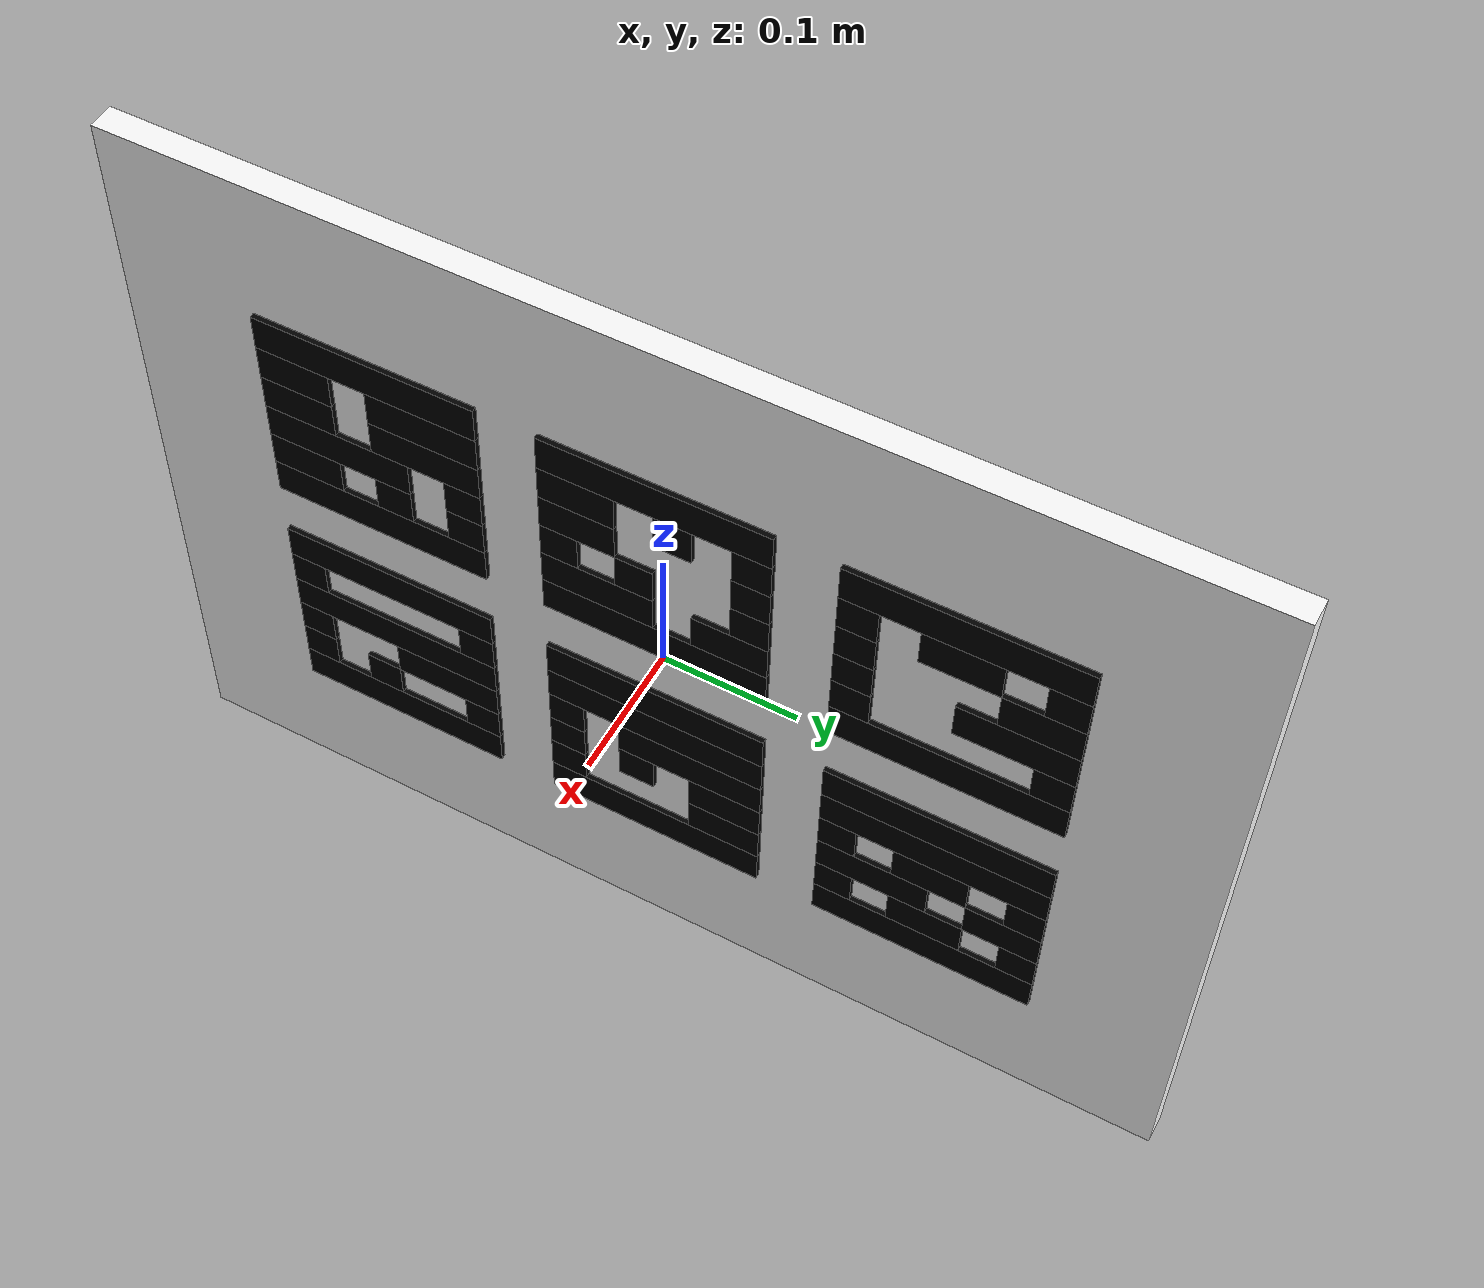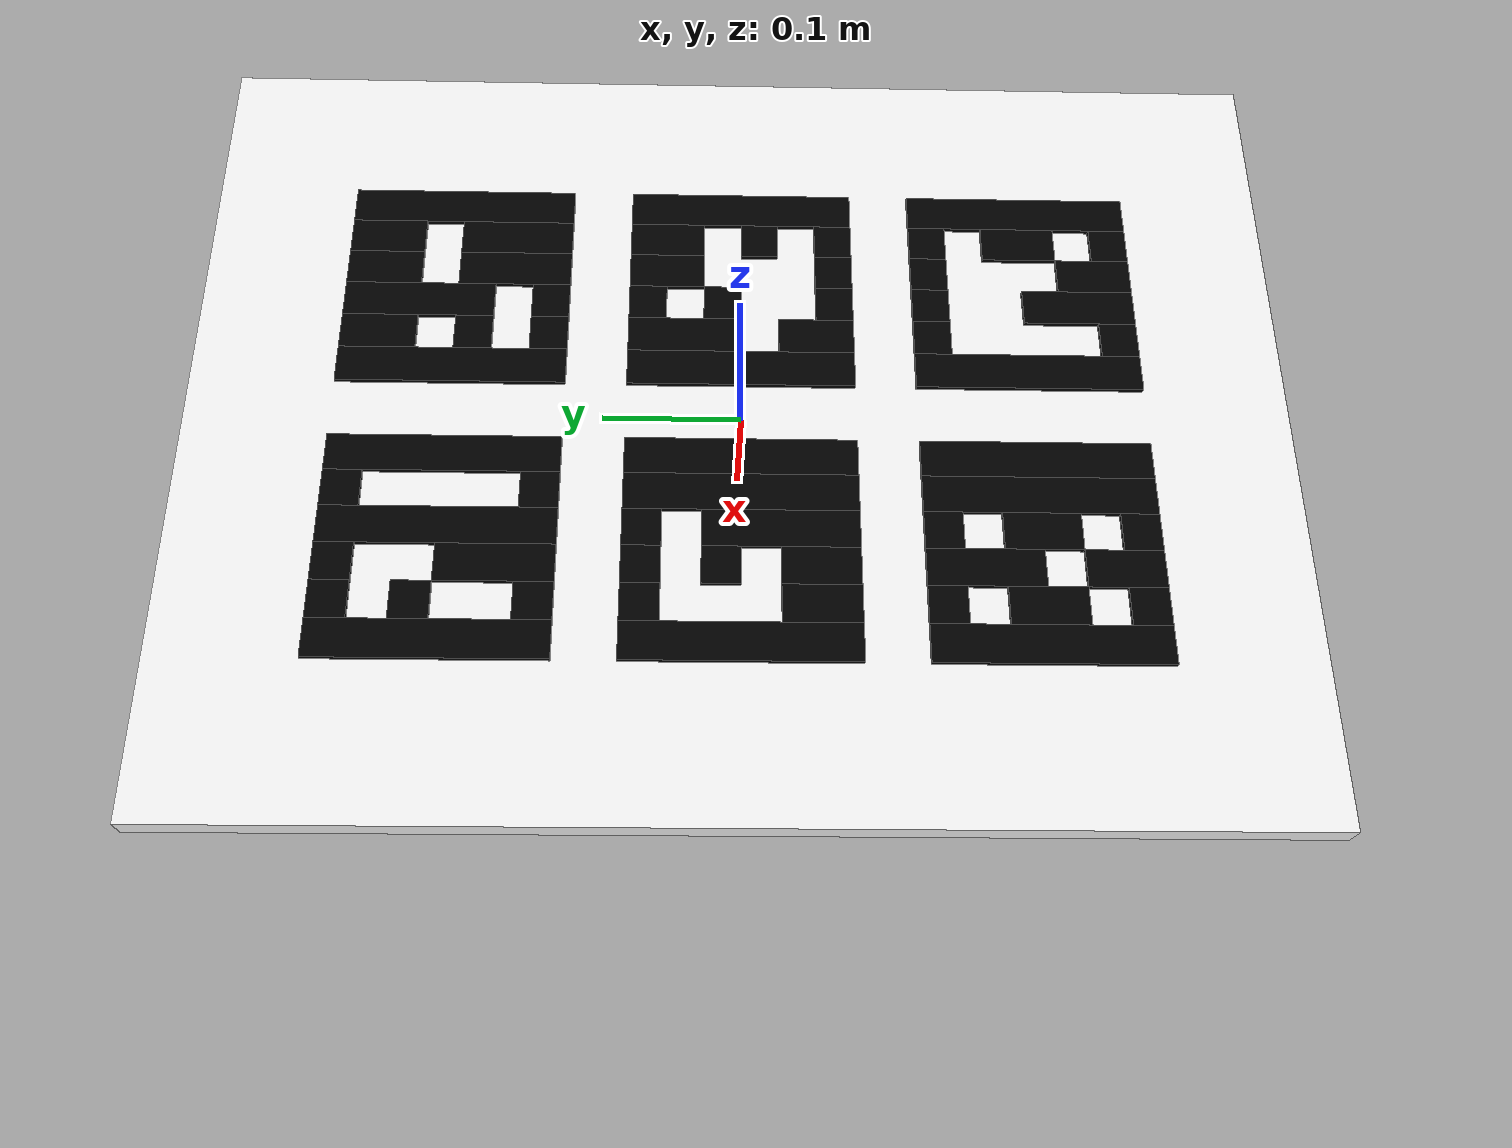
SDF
<?xml version="1.0"?>
<sdf version="1.8">
  <model name="aruco_station_F1_ids_30_35">
    <static>true</static>
    <link name="target_link">

      <visual name="white_board_base">
        <cast_shadows>false</cast_shadows>
        <pose>0.00000000 0.00000000 0.00000000 0.00000000 0.00000000 0.00000000</pose>
        <geometry>
          <box>
            <size>0.02000000 0.80000000 0.60000000</size>
          </box>
        </geometry>
        <material>
          <ambient>1 1 1 1</ambient>
          <diffuse>1 1 1 1</diffuse>
          <specular>0 0 0 1</specular>
          <emissive>1 1 1 1</emissive>
        </material>
      </visual>

      <visual name="black_cell_front_plus_x_id30_r0_c0_6">
        <cast_shadows>false</cast_shadows>
        <pose>0.01300000 -0.21111111 0.17500000 0.00000000 0.00000000 0.00000000</pose>
        <geometry>
          <box>
            <size>0.00400000 0.16666667 0.02777778</size>
          </box>
        </geometry>
        <material>
          <ambient>0 0 0 1</ambient>
          <diffuse>0 0 0 1</diffuse>
          <specular>0 0 0 1</specular>
          <emissive>0 0 0 1</emissive>
        </material>
      </visual>

      <visual name="black_cell_front_plus_x_id30_r1_c0_2">
        <cast_shadows>false</cast_shadows>
        <pose>0.01300000 -0.26666667 0.14722222 0.00000000 0.00000000 0.00000000</pose>
        <geometry>
          <box>
            <size>0.00400000 0.05555556 0.02777778</size>
          </box>
        </geometry>
        <material>
          <ambient>0 0 0 1</ambient>
          <diffuse>0 0 0 1</diffuse>
          <specular>0 0 0 1</specular>
          <emissive>0 0 0 1</emissive>
        </material>
      </visual>

      <visual name="black_cell_front_plus_x_id30_r1_c3_6">
        <cast_shadows>false</cast_shadows>
        <pose>0.01300000 -0.16944444 0.14722222 0.00000000 0.00000000 0.00000000</pose>
        <geometry>
          <box>
            <size>0.00400000 0.08333333 0.02777778</size>
          </box>
        </geometry>
        <material>
          <ambient>0 0 0 1</ambient>
          <diffuse>0 0 0 1</diffuse>
          <specular>0 0 0 1</specular>
          <emissive>0 0 0 1</emissive>
        </material>
      </visual>

      <visual name="black_cell_front_plus_x_id30_r2_c0_2">
        <cast_shadows>false</cast_shadows>
        <pose>0.01300000 -0.26666667 0.11944444 0.00000000 0.00000000 0.00000000</pose>
        <geometry>
          <box>
            <size>0.00400000 0.05555556 0.02777778</size>
          </box>
        </geometry>
        <material>
          <ambient>0 0 0 1</ambient>
          <diffuse>0 0 0 1</diffuse>
          <specular>0 0 0 1</specular>
          <emissive>0 0 0 1</emissive>
        </material>
      </visual>

      <visual name="black_cell_front_plus_x_id30_r2_c3_6">
        <cast_shadows>false</cast_shadows>
        <pose>0.01300000 -0.16944444 0.11944444 0.00000000 0.00000000 0.00000000</pose>
        <geometry>
          <box>
            <size>0.00400000 0.08333333 0.02777778</size>
          </box>
        </geometry>
        <material>
          <ambient>0 0 0 1</ambient>
          <diffuse>0 0 0 1</diffuse>
          <specular>0 0 0 1</specular>
          <emissive>0 0 0 1</emissive>
        </material>
      </visual>

      <visual name="black_cell_front_plus_x_id30_r3_c0_4">
        <cast_shadows>false</cast_shadows>
        <pose>0.01300000 -0.23888889 0.09166667 0.00000000 0.00000000 0.00000000</pose>
        <geometry>
          <box>
            <size>0.00400000 0.11111111 0.02777778</size>
          </box>
        </geometry>
        <material>
          <ambient>0 0 0 1</ambient>
          <diffuse>0 0 0 1</diffuse>
          <specular>0 0 0 1</specular>
          <emissive>0 0 0 1</emissive>
        </material>
      </visual>

      <visual name="black_cell_front_plus_x_id30_r3_c5_6">
        <cast_shadows>false</cast_shadows>
        <pose>0.01300000 -0.14166667 0.09166667 0.00000000 0.00000000 0.00000000</pose>
        <geometry>
          <box>
            <size>0.00400000 0.02777778 0.02777778</size>
          </box>
        </geometry>
        <material>
          <ambient>0 0 0 1</ambient>
          <diffuse>0 0 0 1</diffuse>
          <specular>0 0 0 1</specular>
          <emissive>0 0 0 1</emissive>
        </material>
      </visual>

      <visual name="black_cell_front_plus_x_id30_r4_c0_2">
        <cast_shadows>false</cast_shadows>
        <pose>0.01300000 -0.26666667 0.06388889 0.00000000 0.00000000 0.00000000</pose>
        <geometry>
          <box>
            <size>0.00400000 0.05555556 0.02777778</size>
          </box>
        </geometry>
        <material>
          <ambient>0 0 0 1</ambient>
          <diffuse>0 0 0 1</diffuse>
          <specular>0 0 0 1</specular>
          <emissive>0 0 0 1</emissive>
        </material>
      </visual>

      <visual name="black_cell_front_plus_x_id30_r4_c3_4">
        <cast_shadows>false</cast_shadows>
        <pose>0.01300000 -0.19722222 0.06388889 0.00000000 0.00000000 0.00000000</pose>
        <geometry>
          <box>
            <size>0.00400000 0.02777778 0.02777778</size>
          </box>
        </geometry>
        <material>
          <ambient>0 0 0 1</ambient>
          <diffuse>0 0 0 1</diffuse>
          <specular>0 0 0 1</specular>
          <emissive>0 0 0 1</emissive>
        </material>
      </visual>

      <visual name="black_cell_front_plus_x_id30_r4_c5_6">
        <cast_shadows>false</cast_shadows>
        <pose>0.01300000 -0.14166667 0.06388889 0.00000000 0.00000000 0.00000000</pose>
        <geometry>
          <box>
            <size>0.00400000 0.02777778 0.02777778</size>
          </box>
        </geometry>
        <material>
          <ambient>0 0 0 1</ambient>
          <diffuse>0 0 0 1</diffuse>
          <specular>0 0 0 1</specular>
          <emissive>0 0 0 1</emissive>
        </material>
      </visual>

      <visual name="black_cell_front_plus_x_id30_r5_c0_6">
        <cast_shadows>false</cast_shadows>
        <pose>0.01300000 -0.21111111 0.03611111 0.00000000 0.00000000 0.00000000</pose>
        <geometry>
          <box>
            <size>0.00400000 0.16666667 0.02777778</size>
          </box>
        </geometry>
        <material>
          <ambient>0 0 0 1</ambient>
          <diffuse>0 0 0 1</diffuse>
          <specular>0 0 0 1</specular>
          <emissive>0 0 0 1</emissive>
        </material>
      </visual>

      <visual name="black_cell_back_minus_x_id30_r0_c0_6">
        <cast_shadows>false</cast_shadows>
        <pose>-0.01300000 0.21111111 0.17500000 0.00000000 0.00000000 0.00000000</pose>
        <geometry>
          <box>
            <size>0.00400000 0.16666667 0.02777778</size>
          </box>
        </geometry>
        <material>
          <ambient>0 0 0 1</ambient>
          <diffuse>0 0 0 1</diffuse>
          <specular>0 0 0 1</specular>
          <emissive>0 0 0 1</emissive>
        </material>
      </visual>

      <visual name="black_cell_back_minus_x_id30_r1_c0_2">
        <cast_shadows>false</cast_shadows>
        <pose>-0.01300000 0.26666667 0.14722222 0.00000000 0.00000000 0.00000000</pose>
        <geometry>
          <box>
            <size>0.00400000 0.05555556 0.02777778</size>
          </box>
        </geometry>
        <material>
          <ambient>0 0 0 1</ambient>
          <diffuse>0 0 0 1</diffuse>
          <specular>0 0 0 1</specular>
          <emissive>0 0 0 1</emissive>
        </material>
      </visual>

      <visual name="black_cell_back_minus_x_id30_r1_c3_6">
        <cast_shadows>false</cast_shadows>
        <pose>-0.01300000 0.16944444 0.14722222 0.00000000 0.00000000 0.00000000</pose>
        <geometry>
          <box>
            <size>0.00400000 0.08333333 0.02777778</size>
          </box>
        </geometry>
        <material>
          <ambient>0 0 0 1</ambient>
          <diffuse>0 0 0 1</diffuse>
          <specular>0 0 0 1</specular>
          <emissive>0 0 0 1</emissive>
        </material>
      </visual>

      <visual name="black_cell_back_minus_x_id30_r2_c0_2">
        <cast_shadows>false</cast_shadows>
        <pose>-0.01300000 0.26666667 0.11944444 0.00000000 0.00000000 0.00000000</pose>
        <geometry>
          <box>
            <size>0.00400000 0.05555556 0.02777778</size>
          </box>
        </geometry>
        <material>
          <ambient>0 0 0 1</ambient>
          <diffuse>0 0 0 1</diffuse>
          <specular>0 0 0 1</specular>
          <emissive>0 0 0 1</emissive>
        </material>
      </visual>

      <visual name="black_cell_back_minus_x_id30_r2_c3_6">
        <cast_shadows>false</cast_shadows>
        <pose>-0.01300000 0.16944444 0.11944444 0.00000000 0.00000000 0.00000000</pose>
        <geometry>
          <box>
            <size>0.00400000 0.08333333 0.02777778</size>
          </box>
        </geometry>
        <material>
          <ambient>0 0 0 1</ambient>
          <diffuse>0 0 0 1</diffuse>
          <specular>0 0 0 1</specular>
          <emissive>0 0 0 1</emissive>
        </material>
      </visual>

      <visual name="black_cell_back_minus_x_id30_r3_c0_4">
        <cast_shadows>false</cast_shadows>
        <pose>-0.01300000 0.23888889 0.09166667 0.00000000 0.00000000 0.00000000</pose>
        <geometry>
          <box>
            <size>0.00400000 0.11111111 0.02777778</size>
          </box>
        </geometry>
        <material>
          <ambient>0 0 0 1</ambient>
          <diffuse>0 0 0 1</diffuse>
          <specular>0 0 0 1</specular>
          <emissive>0 0 0 1</emissive>
        </material>
      </visual>

      <visual name="black_cell_back_minus_x_id30_r3_c5_6">
        <cast_shadows>false</cast_shadows>
        <pose>-0.01300000 0.14166667 0.09166667 0.00000000 0.00000000 0.00000000</pose>
        <geometry>
          <box>
            <size>0.00400000 0.02777778 0.02777778</size>
          </box>
        </geometry>
        <material>
          <ambient>0 0 0 1</ambient>
          <diffuse>0 0 0 1</diffuse>
          <specular>0 0 0 1</specular>
          <emissive>0 0 0 1</emissive>
        </material>
      </visual>

      <visual name="black_cell_back_minus_x_id30_r4_c0_2">
        <cast_shadows>false</cast_shadows>
        <pose>-0.01300000 0.26666667 0.06388889 0.00000000 0.00000000 0.00000000</pose>
        <geometry>
          <box>
            <size>0.00400000 0.05555556 0.02777778</size>
          </box>
        </geometry>
        <material>
          <ambient>0 0 0 1</ambient>
          <diffuse>0 0 0 1</diffuse>
          <specular>0 0 0 1</specular>
          <emissive>0 0 0 1</emissive>
        </material>
      </visual>

      <visual name="black_cell_back_minus_x_id30_r4_c3_4">
        <cast_shadows>false</cast_shadows>
        <pose>-0.01300000 0.19722222 0.06388889 0.00000000 0.00000000 0.00000000</pose>
        <geometry>
          <box>
            <size>0.00400000 0.02777778 0.02777778</size>
          </box>
        </geometry>
        <material>
          <ambient>0 0 0 1</ambient>
          <diffuse>0 0 0 1</diffuse>
          <specular>0 0 0 1</specular>
          <emissive>0 0 0 1</emissive>
        </material>
      </visual>

      <visual name="black_cell_back_minus_x_id30_r4_c5_6">
        <cast_shadows>false</cast_shadows>
        <pose>-0.01300000 0.14166667 0.06388889 0.00000000 0.00000000 0.00000000</pose>
        <geometry>
          <box>
            <size>0.00400000 0.02777778 0.02777778</size>
          </box>
        </geometry>
        <material>
          <ambient>0 0 0 1</ambient>
          <diffuse>0 0 0 1</diffuse>
          <specular>0 0 0 1</specular>
          <emissive>0 0 0 1</emissive>
        </material>
      </visual>

      <visual name="black_cell_back_minus_x_id30_r5_c0_6">
        <cast_shadows>false</cast_shadows>
        <pose>-0.01300000 0.21111111 0.03611111 0.00000000 0.00000000 0.00000000</pose>
        <geometry>
          <box>
            <size>0.00400000 0.16666667 0.02777778</size>
          </box>
        </geometry>
        <material>
          <ambient>0 0 0 1</ambient>
          <diffuse>0 0 0 1</diffuse>
          <specular>0 0 0 1</specular>
          <emissive>0 0 0 1</emissive>
        </material>
      </visual>

      <visual name="black_cell_front_plus_x_id31_r0_c0_6">
        <cast_shadows>false</cast_shadows>
        <pose>0.01300000 -0.00000000 0.17500000 0.00000000 0.00000000 0.00000000</pose>
        <geometry>
          <box>
            <size>0.00400000 0.16666667 0.02777778</size>
          </box>
        </geometry>
        <material>
          <ambient>0 0 0 1</ambient>
          <diffuse>0 0 0 1</diffuse>
          <specular>0 0 0 1</specular>
          <emissive>0 0 0 1</emissive>
        </material>
      </visual>

      <visual name="black_cell_front_plus_x_id31_r1_c0_2">
        <cast_shadows>false</cast_shadows>
        <pose>0.01300000 -0.05555556 0.14722222 0.00000000 0.00000000 0.00000000</pose>
        <geometry>
          <box>
            <size>0.00400000 0.05555556 0.02777778</size>
          </box>
        </geometry>
        <material>
          <ambient>0 0 0 1</ambient>
          <diffuse>0 0 0 1</diffuse>
          <specular>0 0 0 1</specular>
          <emissive>0 0 0 1</emissive>
        </material>
      </visual>

      <visual name="black_cell_front_plus_x_id31_r1_c3_4">
        <cast_shadows>false</cast_shadows>
        <pose>0.01300000 0.01388889 0.14722222 0.00000000 0.00000000 0.00000000</pose>
        <geometry>
          <box>
            <size>0.00400000 0.02777778 0.02777778</size>
          </box>
        </geometry>
        <material>
          <ambient>0 0 0 1</ambient>
          <diffuse>0 0 0 1</diffuse>
          <specular>0 0 0 1</specular>
          <emissive>0 0 0 1</emissive>
        </material>
      </visual>

      <visual name="black_cell_front_plus_x_id31_r1_c5_6">
        <cast_shadows>false</cast_shadows>
        <pose>0.01300000 0.06944444 0.14722222 0.00000000 0.00000000 0.00000000</pose>
        <geometry>
          <box>
            <size>0.00400000 0.02777778 0.02777778</size>
          </box>
        </geometry>
        <material>
          <ambient>0 0 0 1</ambient>
          <diffuse>0 0 0 1</diffuse>
          <specular>0 0 0 1</specular>
          <emissive>0 0 0 1</emissive>
        </material>
      </visual>

      <visual name="black_cell_front_plus_x_id31_r2_c0_2">
        <cast_shadows>false</cast_shadows>
        <pose>0.01300000 -0.05555556 0.11944444 0.00000000 0.00000000 0.00000000</pose>
        <geometry>
          <box>
            <size>0.00400000 0.05555556 0.02777778</size>
          </box>
        </geometry>
        <material>
          <ambient>0 0 0 1</ambient>
          <diffuse>0 0 0 1</diffuse>
          <specular>0 0 0 1</specular>
          <emissive>0 0 0 1</emissive>
        </material>
      </visual>

      <visual name="black_cell_front_plus_x_id31_r2_c5_6">
        <cast_shadows>false</cast_shadows>
        <pose>0.01300000 0.06944444 0.11944444 0.00000000 0.00000000 0.00000000</pose>
        <geometry>
          <box>
            <size>0.00400000 0.02777778 0.02777778</size>
          </box>
        </geometry>
        <material>
          <ambient>0 0 0 1</ambient>
          <diffuse>0 0 0 1</diffuse>
          <specular>0 0 0 1</specular>
          <emissive>0 0 0 1</emissive>
        </material>
      </visual>

      <visual name="black_cell_front_plus_x_id31_r3_c0_1">
        <cast_shadows>false</cast_shadows>
        <pose>0.01300000 -0.06944444 0.09166667 0.00000000 0.00000000 0.00000000</pose>
        <geometry>
          <box>
            <size>0.00400000 0.02777778 0.02777778</size>
          </box>
        </geometry>
        <material>
          <ambient>0 0 0 1</ambient>
          <diffuse>0 0 0 1</diffuse>
          <specular>0 0 0 1</specular>
          <emissive>0 0 0 1</emissive>
        </material>
      </visual>

      <visual name="black_cell_front_plus_x_id31_r3_c2_3">
        <cast_shadows>false</cast_shadows>
        <pose>0.01300000 -0.01388889 0.09166667 0.00000000 0.00000000 0.00000000</pose>
        <geometry>
          <box>
            <size>0.00400000 0.02777778 0.02777778</size>
          </box>
        </geometry>
        <material>
          <ambient>0 0 0 1</ambient>
          <diffuse>0 0 0 1</diffuse>
          <specular>0 0 0 1</specular>
          <emissive>0 0 0 1</emissive>
        </material>
      </visual>

      <visual name="black_cell_front_plus_x_id31_r3_c5_6">
        <cast_shadows>false</cast_shadows>
        <pose>0.01300000 0.06944444 0.09166667 0.00000000 0.00000000 0.00000000</pose>
        <geometry>
          <box>
            <size>0.00400000 0.02777778 0.02777778</size>
          </box>
        </geometry>
        <material>
          <ambient>0 0 0 1</ambient>
          <diffuse>0 0 0 1</diffuse>
          <specular>0 0 0 1</specular>
          <emissive>0 0 0 1</emissive>
        </material>
      </visual>

      <visual name="black_cell_front_plus_x_id31_r4_c0_3">
        <cast_shadows>false</cast_shadows>
        <pose>0.01300000 -0.04166667 0.06388889 0.00000000 0.00000000 0.00000000</pose>
        <geometry>
          <box>
            <size>0.00400000 0.08333333 0.02777778</size>
          </box>
        </geometry>
        <material>
          <ambient>0 0 0 1</ambient>
          <diffuse>0 0 0 1</diffuse>
          <specular>0 0 0 1</specular>
          <emissive>0 0 0 1</emissive>
        </material>
      </visual>

      <visual name="black_cell_front_plus_x_id31_r4_c4_6">
        <cast_shadows>false</cast_shadows>
        <pose>0.01300000 0.05555556 0.06388889 0.00000000 0.00000000 0.00000000</pose>
        <geometry>
          <box>
            <size>0.00400000 0.05555556 0.02777778</size>
          </box>
        </geometry>
        <material>
          <ambient>0 0 0 1</ambient>
          <diffuse>0 0 0 1</diffuse>
          <specular>0 0 0 1</specular>
          <emissive>0 0 0 1</emissive>
        </material>
      </visual>

      <visual name="black_cell_front_plus_x_id31_r5_c0_6">
        <cast_shadows>false</cast_shadows>
        <pose>0.01300000 -0.00000000 0.03611111 0.00000000 0.00000000 0.00000000</pose>
        <geometry>
          <box>
            <size>0.00400000 0.16666667 0.02777778</size>
          </box>
        </geometry>
        <material>
          <ambient>0 0 0 1</ambient>
          <diffuse>0 0 0 1</diffuse>
          <specular>0 0 0 1</specular>
          <emissive>0 0 0 1</emissive>
        </material>
      </visual>

      <visual name="black_cell_back_minus_x_id31_r0_c0_6">
        <cast_shadows>false</cast_shadows>
        <pose>-0.01300000 0.00000000 0.17500000 0.00000000 0.00000000 0.00000000</pose>
        <geometry>
          <box>
            <size>0.00400000 0.16666667 0.02777778</size>
          </box>
        </geometry>
        <material>
          <ambient>0 0 0 1</ambient>
          <diffuse>0 0 0 1</diffuse>
          <specular>0 0 0 1</specular>
          <emissive>0 0 0 1</emissive>
        </material>
      </visual>

      <visual name="black_cell_back_minus_x_id31_r1_c0_2">
        <cast_shadows>false</cast_shadows>
        <pose>-0.01300000 0.05555556 0.14722222 0.00000000 0.00000000 0.00000000</pose>
        <geometry>
          <box>
            <size>0.00400000 0.05555556 0.02777778</size>
          </box>
        </geometry>
        <material>
          <ambient>0 0 0 1</ambient>
          <diffuse>0 0 0 1</diffuse>
          <specular>0 0 0 1</specular>
          <emissive>0 0 0 1</emissive>
        </material>
      </visual>

      <visual name="black_cell_back_minus_x_id31_r1_c3_4">
        <cast_shadows>false</cast_shadows>
        <pose>-0.01300000 -0.01388889 0.14722222 0.00000000 0.00000000 0.00000000</pose>
        <geometry>
          <box>
            <size>0.00400000 0.02777778 0.02777778</size>
          </box>
        </geometry>
        <material>
          <ambient>0 0 0 1</ambient>
          <diffuse>0 0 0 1</diffuse>
          <specular>0 0 0 1</specular>
          <emissive>0 0 0 1</emissive>
        </material>
      </visual>

      <visual name="black_cell_back_minus_x_id31_r1_c5_6">
        <cast_shadows>false</cast_shadows>
        <pose>-0.01300000 -0.06944444 0.14722222 0.00000000 0.00000000 0.00000000</pose>
        <geometry>
          <box>
            <size>0.00400000 0.02777778 0.02777778</size>
          </box>
        </geometry>
        <material>
          <ambient>0 0 0 1</ambient>
          <diffuse>0 0 0 1</diffuse>
          <specular>0 0 0 1</specular>
          <emissive>0 0 0 1</emissive>
        </material>
      </visual>

      <visual name="black_cell_back_minus_x_id31_r2_c0_2">
        <cast_shadows>false</cast_shadows>
        <pose>-0.01300000 0.05555556 0.11944444 0.00000000 0.00000000 0.00000000</pose>
        <geometry>
          <box>
            <size>0.00400000 0.05555556 0.02777778</size>
          </box>
        </geometry>
        <material>
          <ambient>0 0 0 1</ambient>
          <diffuse>0 0 0 1</diffuse>
          <specular>0 0 0 1</specular>
          <emissive>0 0 0 1</emissive>
        </material>
      </visual>

      <visual name="black_cell_back_minus_x_id31_r2_c5_6">
        <cast_shadows>false</cast_shadows>
        <pose>-0.01300000 -0.06944444 0.11944444 0.00000000 0.00000000 0.00000000</pose>
        <geometry>
          <box>
            <size>0.00400000 0.02777778 0.02777778</size>
          </box>
        </geometry>
        <material>
          <ambient>0 0 0 1</ambient>
          <diffuse>0 0 0 1</diffuse>
          <specular>0 0 0 1</specular>
          <emissive>0 0 0 1</emissive>
        </material>
      </visual>

      <visual name="black_cell_back_minus_x_id31_r3_c0_1">
        <cast_shadows>false</cast_shadows>
        <pose>-0.01300000 0.06944444 0.09166667 0.00000000 0.00000000 0.00000000</pose>
        <geometry>
          <box>
            <size>0.00400000 0.02777778 0.02777778</size>
          </box>
        </geometry>
        <material>
          <ambient>0 0 0 1</ambient>
          <diffuse>0 0 0 1</diffuse>
          <specular>0 0 0 1</specular>
          <emissive>0 0 0 1</emissive>
        </material>
      </visual>

      <visual name="black_cell_back_minus_x_id31_r3_c2_3">
        <cast_shadows>false</cast_shadows>
        <pose>-0.01300000 0.01388889 0.09166667 0.00000000 0.00000000 0.00000000</pose>
        <geometry>
          <box>
            <size>0.00400000 0.02777778 0.02777778</size>
          </box>
        </geometry>
        <material>
          <ambient>0 0 0 1</ambient>
          <diffuse>0 0 0 1</diffuse>
          <specular>0 0 0 1</specular>
          <emissive>0 0 0 1</emissive>
        </material>
      </visual>

      <visual name="black_cell_back_minus_x_id31_r3_c5_6">
        <cast_shadows>false</cast_shadows>
        <pose>-0.01300000 -0.06944444 0.09166667 0.00000000 0.00000000 0.00000000</pose>
        <geometry>
          <box>
            <size>0.00400000 0.02777778 0.02777778</size>
          </box>
        </geometry>
        <material>
          <ambient>0 0 0 1</ambient>
          <diffuse>0 0 0 1</diffuse>
          <specular>0 0 0 1</specular>
          <emissive>0 0 0 1</emissive>
        </material>
      </visual>

      <visual name="black_cell_back_minus_x_id31_r4_c0_3">
        <cast_shadows>false</cast_shadows>
        <pose>-0.01300000 0.04166667 0.06388889 0.00000000 0.00000000 0.00000000</pose>
        <geometry>
          <box>
            <size>0.00400000 0.08333333 0.02777778</size>
          </box>
        </geometry>
        <material>
          <ambient>0 0 0 1</ambient>
          <diffuse>0 0 0 1</diffuse>
          <specular>0 0 0 1</specular>
          <emissive>0 0 0 1</emissive>
        </material>
      </visual>

      <visual name="black_cell_back_minus_x_id31_r4_c4_6">
        <cast_shadows>false</cast_shadows>
        <pose>-0.01300000 -0.05555556 0.06388889 0.00000000 0.00000000 0.00000000</pose>
        <geometry>
          <box>
            <size>0.00400000 0.05555556 0.02777778</size>
          </box>
        </geometry>
        <material>
          <ambient>0 0 0 1</ambient>
          <diffuse>0 0 0 1</diffuse>
          <specular>0 0 0 1</specular>
          <emissive>0 0 0 1</emissive>
        </material>
      </visual>

      <visual name="black_cell_back_minus_x_id31_r5_c0_6">
        <cast_shadows>false</cast_shadows>
        <pose>-0.01300000 0.00000000 0.03611111 0.00000000 0.00000000 0.00000000</pose>
        <geometry>
          <box>
            <size>0.00400000 0.16666667 0.02777778</size>
          </box>
        </geometry>
        <material>
          <ambient>0 0 0 1</ambient>
          <diffuse>0 0 0 1</diffuse>
          <specular>0 0 0 1</specular>
          <emissive>0 0 0 1</emissive>
        </material>
      </visual>

      <visual name="black_cell_front_plus_x_id32_r0_c0_6">
        <cast_shadows>false</cast_shadows>
        <pose>0.01300000 0.21111111 0.17500000 0.00000000 0.00000000 0.00000000</pose>
        <geometry>
          <box>
            <size>0.00400000 0.16666667 0.02777778</size>
          </box>
        </geometry>
        <material>
          <ambient>0 0 0 1</ambient>
          <diffuse>0 0 0 1</diffuse>
          <specular>0 0 0 1</specular>
          <emissive>0 0 0 1</emissive>
        </material>
      </visual>

      <visual name="black_cell_front_plus_x_id32_r1_c0_1">
        <cast_shadows>false</cast_shadows>
        <pose>0.01300000 0.14166667 0.14722222 0.00000000 0.00000000 0.00000000</pose>
        <geometry>
          <box>
            <size>0.00400000 0.02777778 0.02777778</size>
          </box>
        </geometry>
        <material>
          <ambient>0 0 0 1</ambient>
          <diffuse>0 0 0 1</diffuse>
          <specular>0 0 0 1</specular>
          <emissive>0 0 0 1</emissive>
        </material>
      </visual>

      <visual name="black_cell_front_plus_x_id32_r1_c2_4">
        <cast_shadows>false</cast_shadows>
        <pose>0.01300000 0.21111111 0.14722222 0.00000000 0.00000000 0.00000000</pose>
        <geometry>
          <box>
            <size>0.00400000 0.05555556 0.02777778</size>
          </box>
        </geometry>
        <material>
          <ambient>0 0 0 1</ambient>
          <diffuse>0 0 0 1</diffuse>
          <specular>0 0 0 1</specular>
          <emissive>0 0 0 1</emissive>
        </material>
      </visual>

      <visual name="black_cell_front_plus_x_id32_r1_c5_6">
        <cast_shadows>false</cast_shadows>
        <pose>0.01300000 0.28055556 0.14722222 0.00000000 0.00000000 0.00000000</pose>
        <geometry>
          <box>
            <size>0.00400000 0.02777778 0.02777778</size>
          </box>
        </geometry>
        <material>
          <ambient>0 0 0 1</ambient>
          <diffuse>0 0 0 1</diffuse>
          <specular>0 0 0 1</specular>
          <emissive>0 0 0 1</emissive>
        </material>
      </visual>

      <visual name="black_cell_front_plus_x_id32_r2_c0_1">
        <cast_shadows>false</cast_shadows>
        <pose>0.01300000 0.14166667 0.11944444 0.00000000 0.00000000 0.00000000</pose>
        <geometry>
          <box>
            <size>0.00400000 0.02777778 0.02777778</size>
          </box>
        </geometry>
        <material>
          <ambient>0 0 0 1</ambient>
          <diffuse>0 0 0 1</diffuse>
          <specular>0 0 0 1</specular>
          <emissive>0 0 0 1</emissive>
        </material>
      </visual>

      <visual name="black_cell_front_plus_x_id32_r2_c4_6">
        <cast_shadows>false</cast_shadows>
        <pose>0.01300000 0.26666667 0.11944444 0.00000000 0.00000000 0.00000000</pose>
        <geometry>
          <box>
            <size>0.00400000 0.05555556 0.02777778</size>
          </box>
        </geometry>
        <material>
          <ambient>0 0 0 1</ambient>
          <diffuse>0 0 0 1</diffuse>
          <specular>0 0 0 1</specular>
          <emissive>0 0 0 1</emissive>
        </material>
      </visual>

      <visual name="black_cell_front_plus_x_id32_r3_c0_1">
        <cast_shadows>false</cast_shadows>
        <pose>0.01300000 0.14166667 0.09166667 0.00000000 0.00000000 0.00000000</pose>
        <geometry>
          <box>
            <size>0.00400000 0.02777778 0.02777778</size>
          </box>
        </geometry>
        <material>
          <ambient>0 0 0 1</ambient>
          <diffuse>0 0 0 1</diffuse>
          <specular>0 0 0 1</specular>
          <emissive>0 0 0 1</emissive>
        </material>
      </visual>

      <visual name="black_cell_front_plus_x_id32_r3_c3_6">
        <cast_shadows>false</cast_shadows>
        <pose>0.01300000 0.25277778 0.09166667 0.00000000 0.00000000 0.00000000</pose>
        <geometry>
          <box>
            <size>0.00400000 0.08333333 0.02777778</size>
          </box>
        </geometry>
        <material>
          <ambient>0 0 0 1</ambient>
          <diffuse>0 0 0 1</diffuse>
          <specular>0 0 0 1</specular>
          <emissive>0 0 0 1</emissive>
        </material>
      </visual>

      <visual name="black_cell_front_plus_x_id32_r4_c0_1">
        <cast_shadows>false</cast_shadows>
        <pose>0.01300000 0.14166667 0.06388889 0.00000000 0.00000000 0.00000000</pose>
        <geometry>
          <box>
            <size>0.00400000 0.02777778 0.02777778</size>
          </box>
        </geometry>
        <material>
          <ambient>0 0 0 1</ambient>
          <diffuse>0 0 0 1</diffuse>
          <specular>0 0 0 1</specular>
          <emissive>0 0 0 1</emissive>
        </material>
      </visual>

      <visual name="black_cell_front_plus_x_id32_r4_c5_6">
        <cast_shadows>false</cast_shadows>
        <pose>0.01300000 0.28055556 0.06388889 0.00000000 0.00000000 0.00000000</pose>
        <geometry>
          <box>
            <size>0.00400000 0.02777778 0.02777778</size>
          </box>
        </geometry>
        <material>
          <ambient>0 0 0 1</ambient>
          <diffuse>0 0 0 1</diffuse>
          <specular>0 0 0 1</specular>
          <emissive>0 0 0 1</emissive>
        </material>
      </visual>

      <visual name="black_cell_front_plus_x_id32_r5_c0_6">
        <cast_shadows>false</cast_shadows>
        <pose>0.01300000 0.21111111 0.03611111 0.00000000 0.00000000 0.00000000</pose>
        <geometry>
          <box>
            <size>0.00400000 0.16666667 0.02777778</size>
          </box>
        </geometry>
        <material>
          <ambient>0 0 0 1</ambient>
          <diffuse>0 0 0 1</diffuse>
          <specular>0 0 0 1</specular>
          <emissive>0 0 0 1</emissive>
        </material>
      </visual>

      <visual name="black_cell_back_minus_x_id32_r0_c0_6">
        <cast_shadows>false</cast_shadows>
        <pose>-0.01300000 -0.21111111 0.17500000 0.00000000 0.00000000 0.00000000</pose>
        <geometry>
          <box>
            <size>0.00400000 0.16666667 0.02777778</size>
          </box>
        </geometry>
        <material>
          <ambient>0 0 0 1</ambient>
          <diffuse>0 0 0 1</diffuse>
          <specular>0 0 0 1</specular>
          <emissive>0 0 0 1</emissive>
        </material>
      </visual>

      <visual name="black_cell_back_minus_x_id32_r1_c0_1">
        <cast_shadows>false</cast_shadows>
        <pose>-0.01300000 -0.14166667 0.14722222 0.00000000 0.00000000 0.00000000</pose>
        <geometry>
          <box>
            <size>0.00400000 0.02777778 0.02777778</size>
          </box>
        </geometry>
        <material>
          <ambient>0 0 0 1</ambient>
          <diffuse>0 0 0 1</diffuse>
          <specular>0 0 0 1</specular>
          <emissive>0 0 0 1</emissive>
        </material>
      </visual>

      <visual name="black_cell_back_minus_x_id32_r1_c2_4">
        <cast_shadows>false</cast_shadows>
        <pose>-0.01300000 -0.21111111 0.14722222 0.00000000 0.00000000 0.00000000</pose>
        <geometry>
          <box>
            <size>0.00400000 0.05555556 0.02777778</size>
          </box>
        </geometry>
        <material>
          <ambient>0 0 0 1</ambient>
          <diffuse>0 0 0 1</diffuse>
          <specular>0 0 0 1</specular>
          <emissive>0 0 0 1</emissive>
        </material>
      </visual>

      <visual name="black_cell_back_minus_x_id32_r1_c5_6">
        <cast_shadows>false</cast_shadows>
        <pose>-0.01300000 -0.28055556 0.14722222 0.00000000 0.00000000 0.00000000</pose>
        <geometry>
          <box>
            <size>0.00400000 0.02777778 0.02777778</size>
          </box>
        </geometry>
        <material>
          <ambient>0 0 0 1</ambient>
          <diffuse>0 0 0 1</diffuse>
          <specular>0 0 0 1</specular>
          <emissive>0 0 0 1</emissive>
        </material>
      </visual>

      <visual name="black_cell_back_minus_x_id32_r2_c0_1">
        <cast_shadows>false</cast_shadows>
        <pose>-0.01300000 -0.14166667 0.11944444 0.00000000 0.00000000 0.00000000</pose>
        <geometry>
          <box>
            <size>0.00400000 0.02777778 0.02777778</size>
          </box>
        </geometry>
        <material>
          <ambient>0 0 0 1</ambient>
          <diffuse>0 0 0 1</diffuse>
          <specular>0 0 0 1</specular>
          <emissive>0 0 0 1</emissive>
        </material>
      </visual>

      <visual name="black_cell_back_minus_x_id32_r2_c4_6">
        <cast_shadows>false</cast_shadows>
        <pose>-0.01300000 -0.26666667 0.11944444 0.00000000 0.00000000 0.00000000</pose>
        <geometry>
          <box>
            <size>0.00400000 0.05555556 0.02777778</size>
          </box>
        </geometry>
        <material>
          <ambient>0 0 0 1</ambient>
          <diffuse>0 0 0 1</diffuse>
          <specular>0 0 0 1</specular>
          <emissive>0 0 0 1</emissive>
        </material>
      </visual>

      <visual name="black_cell_back_minus_x_id32_r3_c0_1">
        <cast_shadows>false</cast_shadows>
        <pose>-0.01300000 -0.14166667 0.09166667 0.00000000 0.00000000 0.00000000</pose>
        <geometry>
          <box>
            <size>0.00400000 0.02777778 0.02777778</size>
          </box>
        </geometry>
        <material>
          <ambient>0 0 0 1</ambient>
          <diffuse>0 0 0 1</diffuse>
          <specular>0 0 0 1</specular>
          <emissive>0 0 0 1</emissive>
        </material>
      </visual>

      <visual name="black_cell_back_minus_x_id32_r3_c3_6">
        <cast_shadows>false</cast_shadows>
        <pose>-0.01300000 -0.25277778 0.09166667 0.00000000 0.00000000 0.00000000</pose>
        <geometry>
          <box>
            <size>0.00400000 0.08333333 0.02777778</size>
          </box>
        </geometry>
        <material>
          <ambient>0 0 0 1</ambient>
          <diffuse>0 0 0 1</diffuse>
          <specular>0 0 0 1</specular>
          <emissive>0 0 0 1</emissive>
        </material>
      </visual>

      <visual name="black_cell_back_minus_x_id32_r4_c0_1">
        <cast_shadows>false</cast_shadows>
        <pose>-0.01300000 -0.14166667 0.06388889 0.00000000 0.00000000 0.00000000</pose>
        <geometry>
          <box>
            <size>0.00400000 0.02777778 0.02777778</size>
          </box>
        </geometry>
        <material>
          <ambient>0 0 0 1</ambient>
          <diffuse>0 0 0 1</diffuse>
          <specular>0 0 0 1</specular>
          <emissive>0 0 0 1</emissive>
        </material>
      </visual>

      <visual name="black_cell_back_minus_x_id32_r4_c5_6">
        <cast_shadows>false</cast_shadows>
        <pose>-0.01300000 -0.28055556 0.06388889 0.00000000 0.00000000 0.00000000</pose>
        <geometry>
          <box>
            <size>0.00400000 0.02777778 0.02777778</size>
          </box>
        </geometry>
        <material>
          <ambient>0 0 0 1</ambient>
          <diffuse>0 0 0 1</diffuse>
          <specular>0 0 0 1</specular>
          <emissive>0 0 0 1</emissive>
        </material>
      </visual>

      <visual name="black_cell_back_minus_x_id32_r5_c0_6">
        <cast_shadows>false</cast_shadows>
        <pose>-0.01300000 -0.21111111 0.03611111 0.00000000 0.00000000 0.00000000</pose>
        <geometry>
          <box>
            <size>0.00400000 0.16666667 0.02777778</size>
          </box>
        </geometry>
        <material>
          <ambient>0 0 0 1</ambient>
          <diffuse>0 0 0 1</diffuse>
          <specular>0 0 0 1</specular>
          <emissive>0 0 0 1</emissive>
        </material>
      </visual>

      <visual name="black_cell_front_plus_x_id33_r0_c0_6">
        <cast_shadows>false</cast_shadows>
        <pose>0.01300000 -0.21111111 -0.03611111 0.00000000 0.00000000 0.00000000</pose>
        <geometry>
          <box>
            <size>0.00400000 0.16666667 0.02777778</size>
          </box>
        </geometry>
        <material>
          <ambient>0 0 0 1</ambient>
          <diffuse>0 0 0 1</diffuse>
          <specular>0 0 0 1</specular>
          <emissive>0 0 0 1</emissive>
        </material>
      </visual>

      <visual name="black_cell_front_plus_x_id33_r1_c0_1">
        <cast_shadows>false</cast_shadows>
        <pose>0.01300000 -0.28055556 -0.06388889 0.00000000 0.00000000 0.00000000</pose>
        <geometry>
          <box>
            <size>0.00400000 0.02777778 0.02777778</size>
          </box>
        </geometry>
        <material>
          <ambient>0 0 0 1</ambient>
          <diffuse>0 0 0 1</diffuse>
          <specular>0 0 0 1</specular>
          <emissive>0 0 0 1</emissive>
        </material>
      </visual>

      <visual name="black_cell_front_plus_x_id33_r1_c5_6">
        <cast_shadows>false</cast_shadows>
        <pose>0.01300000 -0.14166667 -0.06388889 0.00000000 0.00000000 0.00000000</pose>
        <geometry>
          <box>
            <size>0.00400000 0.02777778 0.02777778</size>
          </box>
        </geometry>
        <material>
          <ambient>0 0 0 1</ambient>
          <diffuse>0 0 0 1</diffuse>
          <specular>0 0 0 1</specular>
          <emissive>0 0 0 1</emissive>
        </material>
      </visual>

      <visual name="black_cell_front_plus_x_id33_r2_c0_6">
        <cast_shadows>false</cast_shadows>
        <pose>0.01300000 -0.21111111 -0.09166667 0.00000000 0.00000000 0.00000000</pose>
        <geometry>
          <box>
            <size>0.00400000 0.16666667 0.02777778</size>
          </box>
        </geometry>
        <material>
          <ambient>0 0 0 1</ambient>
          <diffuse>0 0 0 1</diffuse>
          <specular>0 0 0 1</specular>
          <emissive>0 0 0 1</emissive>
        </material>
      </visual>

      <visual name="black_cell_front_plus_x_id33_r3_c0_1">
        <cast_shadows>false</cast_shadows>
        <pose>0.01300000 -0.28055556 -0.11944444 0.00000000 0.00000000 0.00000000</pose>
        <geometry>
          <box>
            <size>0.00400000 0.02777778 0.02777778</size>
          </box>
        </geometry>
        <material>
          <ambient>0 0 0 1</ambient>
          <diffuse>0 0 0 1</diffuse>
          <specular>0 0 0 1</specular>
          <emissive>0 0 0 1</emissive>
        </material>
      </visual>

      <visual name="black_cell_front_plus_x_id33_r3_c3_6">
        <cast_shadows>false</cast_shadows>
        <pose>0.01300000 -0.16944444 -0.11944444 0.00000000 0.00000000 0.00000000</pose>
        <geometry>
          <box>
            <size>0.00400000 0.08333333 0.02777778</size>
          </box>
        </geometry>
        <material>
          <ambient>0 0 0 1</ambient>
          <diffuse>0 0 0 1</diffuse>
          <specular>0 0 0 1</specular>
          <emissive>0 0 0 1</emissive>
        </material>
      </visual>

      <visual name="black_cell_front_plus_x_id33_r4_c0_1">
        <cast_shadows>false</cast_shadows>
        <pose>0.01300000 -0.28055556 -0.14722222 0.00000000 0.00000000 0.00000000</pose>
        <geometry>
          <box>
            <size>0.00400000 0.02777778 0.02777778</size>
          </box>
        </geometry>
        <material>
          <ambient>0 0 0 1</ambient>
          <diffuse>0 0 0 1</diffuse>
          <specular>0 0 0 1</specular>
          <emissive>0 0 0 1</emissive>
        </material>
      </visual>

      <visual name="black_cell_front_plus_x_id33_r4_c2_3">
        <cast_shadows>false</cast_shadows>
        <pose>0.01300000 -0.22500000 -0.14722222 0.00000000 0.00000000 0.00000000</pose>
        <geometry>
          <box>
            <size>0.00400000 0.02777778 0.02777778</size>
          </box>
        </geometry>
        <material>
          <ambient>0 0 0 1</ambient>
          <diffuse>0 0 0 1</diffuse>
          <specular>0 0 0 1</specular>
          <emissive>0 0 0 1</emissive>
        </material>
      </visual>

      <visual name="black_cell_front_plus_x_id33_r4_c5_6">
        <cast_shadows>false</cast_shadows>
        <pose>0.01300000 -0.14166667 -0.14722222 0.00000000 0.00000000 0.00000000</pose>
        <geometry>
          <box>
            <size>0.00400000 0.02777778 0.02777778</size>
          </box>
        </geometry>
        <material>
          <ambient>0 0 0 1</ambient>
          <diffuse>0 0 0 1</diffuse>
          <specular>0 0 0 1</specular>
          <emissive>0 0 0 1</emissive>
        </material>
      </visual>

      <visual name="black_cell_front_plus_x_id33_r5_c0_6">
        <cast_shadows>false</cast_shadows>
        <pose>0.01300000 -0.21111111 -0.17500000 0.00000000 0.00000000 0.00000000</pose>
        <geometry>
          <box>
            <size>0.00400000 0.16666667 0.02777778</size>
          </box>
        </geometry>
        <material>
          <ambient>0 0 0 1</ambient>
          <diffuse>0 0 0 1</diffuse>
          <specular>0 0 0 1</specular>
          <emissive>0 0 0 1</emissive>
        </material>
      </visual>

      <visual name="black_cell_back_minus_x_id33_r0_c0_6">
        <cast_shadows>false</cast_shadows>
        <pose>-0.01300000 0.21111111 -0.03611111 0.00000000 0.00000000 0.00000000</pose>
        <geometry>
          <box>
            <size>0.00400000 0.16666667 0.02777778</size>
          </box>
        </geometry>
        <material>
          <ambient>0 0 0 1</ambient>
          <diffuse>0 0 0 1</diffuse>
          <specular>0 0 0 1</specular>
          <emissive>0 0 0 1</emissive>
        </material>
      </visual>

      <visual name="black_cell_back_minus_x_id33_r1_c0_1">
        <cast_shadows>false</cast_shadows>
        <pose>-0.01300000 0.28055556 -0.06388889 0.00000000 0.00000000 0.00000000</pose>
        <geometry>
          <box>
            <size>0.00400000 0.02777778 0.02777778</size>
          </box>
        </geometry>
        <material>
          <ambient>0 0 0 1</ambient>
          <diffuse>0 0 0 1</diffuse>
          <specular>0 0 0 1</specular>
          <emissive>0 0 0 1</emissive>
        </material>
      </visual>

      <visual name="black_cell_back_minus_x_id33_r1_c5_6">
        <cast_shadows>false</cast_shadows>
        <pose>-0.01300000 0.14166667 -0.06388889 0.00000000 0.00000000 0.00000000</pose>
        <geometry>
          <box>
            <size>0.00400000 0.02777778 0.02777778</size>
          </box>
        </geometry>
        <material>
          <ambient>0 0 0 1</ambient>
          <diffuse>0 0 0 1</diffuse>
          <specular>0 0 0 1</specular>
          <emissive>0 0 0 1</emissive>
        </material>
      </visual>

      <visual name="black_cell_back_minus_x_id33_r2_c0_6">
        <cast_shadows>false</cast_shadows>
        <pose>-0.01300000 0.21111111 -0.09166667 0.00000000 0.00000000 0.00000000</pose>
        <geometry>
          <box>
            <size>0.00400000 0.16666667 0.02777778</size>
          </box>
        </geometry>
        <material>
          <ambient>0 0 0 1</ambient>
          <diffuse>0 0 0 1</diffuse>
          <specular>0 0 0 1</specular>
          <emissive>0 0 0 1</emissive>
        </material>
      </visual>

      <visual name="black_cell_back_minus_x_id33_r3_c0_1">
        <cast_shadows>false</cast_shadows>
        <pose>-0.01300000 0.28055556 -0.11944444 0.00000000 0.00000000 0.00000000</pose>
        <geometry>
          <box>
            <size>0.00400000 0.02777778 0.02777778</size>
          </box>
        </geometry>
        <material>
          <ambient>0 0 0 1</ambient>
          <diffuse>0 0 0 1</diffuse>
          <specular>0 0 0 1</specular>
          <emissive>0 0 0 1</emissive>
        </material>
      </visual>

      <visual name="black_cell_back_minus_x_id33_r3_c3_6">
        <cast_shadows>false</cast_shadows>
        <pose>-0.01300000 0.16944444 -0.11944444 0.00000000 0.00000000 0.00000000</pose>
        <geometry>
          <box>
            <size>0.00400000 0.08333333 0.02777778</size>
          </box>
        </geometry>
        <material>
          <ambient>0 0 0 1</ambient>
          <diffuse>0 0 0 1</diffuse>
          <specular>0 0 0 1</specular>
          <emissive>0 0 0 1</emissive>
        </material>
      </visual>

      <visual name="black_cell_back_minus_x_id33_r4_c0_1">
        <cast_shadows>false</cast_shadows>
        <pose>-0.01300000 0.28055556 -0.14722222 0.00000000 0.00000000 0.00000000</pose>
        <geometry>
          <box>
            <size>0.00400000 0.02777778 0.02777778</size>
          </box>
        </geometry>
        <material>
          <ambient>0 0 0 1</ambient>
          <diffuse>0 0 0 1</diffuse>
          <specular>0 0 0 1</specular>
          <emissive>0 0 0 1</emissive>
        </material>
      </visual>

      <visual name="black_cell_back_minus_x_id33_r4_c2_3">
        <cast_shadows>false</cast_shadows>
        <pose>-0.01300000 0.22500000 -0.14722222 0.00000000 0.00000000 0.00000000</pose>
        <geometry>
          <box>
            <size>0.00400000 0.02777778 0.02777778</size>
          </box>
        </geometry>
        <material>
          <ambient>0 0 0 1</ambient>
          <diffuse>0 0 0 1</diffuse>
          <specular>0 0 0 1</specular>
          <emissive>0 0 0 1</emissive>
        </material>
      </visual>

      <visual name="black_cell_back_minus_x_id33_r4_c5_6">
        <cast_shadows>false</cast_shadows>
        <pose>-0.01300000 0.14166667 -0.14722222 0.00000000 0.00000000 0.00000000</pose>
        <geometry>
          <box>
            <size>0.00400000 0.02777778 0.02777778</size>
          </box>
        </geometry>
        <material>
          <ambient>0 0 0 1</ambient>
          <diffuse>0 0 0 1</diffuse>
          <specular>0 0 0 1</specular>
          <emissive>0 0 0 1</emissive>
        </material>
      </visual>

      <visual name="black_cell_back_minus_x_id33_r5_c0_6">
        <cast_shadows>false</cast_shadows>
        <pose>-0.01300000 0.21111111 -0.17500000 0.00000000 0.00000000 0.00000000</pose>
        <geometry>
          <box>
            <size>0.00400000 0.16666667 0.02777778</size>
          </box>
        </geometry>
        <material>
          <ambient>0 0 0 1</ambient>
          <diffuse>0 0 0 1</diffuse>
          <specular>0 0 0 1</specular>
          <emissive>0 0 0 1</emissive>
        </material>
      </visual>

      <visual name="black_cell_front_plus_x_id34_r0_c0_6">
        <cast_shadows>false</cast_shadows>
        <pose>0.01300000 -0.00000000 -0.03611111 0.00000000 0.00000000 0.00000000</pose>
        <geometry>
          <box>
            <size>0.00400000 0.16666667 0.02777778</size>
          </box>
        </geometry>
        <material>
          <ambient>0 0 0 1</ambient>
          <diffuse>0 0 0 1</diffuse>
          <specular>0 0 0 1</specular>
          <emissive>0 0 0 1</emissive>
        </material>
      </visual>

      <visual name="black_cell_front_plus_x_id34_r1_c0_6">
        <cast_shadows>false</cast_shadows>
        <pose>0.01300000 -0.00000000 -0.06388889 0.00000000 0.00000000 0.00000000</pose>
        <geometry>
          <box>
            <size>0.00400000 0.16666667 0.02777778</size>
          </box>
        </geometry>
        <material>
          <ambient>0 0 0 1</ambient>
          <diffuse>0 0 0 1</diffuse>
          <specular>0 0 0 1</specular>
          <emissive>0 0 0 1</emissive>
        </material>
      </visual>

      <visual name="black_cell_front_plus_x_id34_r2_c0_1">
        <cast_shadows>false</cast_shadows>
        <pose>0.01300000 -0.06944444 -0.09166667 0.00000000 0.00000000 0.00000000</pose>
        <geometry>
          <box>
            <size>0.00400000 0.02777778 0.02777778</size>
          </box>
        </geometry>
        <material>
          <ambient>0 0 0 1</ambient>
          <diffuse>0 0 0 1</diffuse>
          <specular>0 0 0 1</specular>
          <emissive>0 0 0 1</emissive>
        </material>
      </visual>

      <visual name="black_cell_front_plus_x_id34_r2_c2_6">
        <cast_shadows>false</cast_shadows>
        <pose>0.01300000 0.02777778 -0.09166667 0.00000000 0.00000000 0.00000000</pose>
        <geometry>
          <box>
            <size>0.00400000 0.11111111 0.02777778</size>
          </box>
        </geometry>
        <material>
          <ambient>0 0 0 1</ambient>
          <diffuse>0 0 0 1</diffuse>
          <specular>0 0 0 1</specular>
          <emissive>0 0 0 1</emissive>
        </material>
      </visual>

      <visual name="black_cell_front_plus_x_id34_r3_c0_1">
        <cast_shadows>false</cast_shadows>
        <pose>0.01300000 -0.06944444 -0.11944444 0.00000000 0.00000000 0.00000000</pose>
        <geometry>
          <box>
            <size>0.00400000 0.02777778 0.02777778</size>
          </box>
        </geometry>
        <material>
          <ambient>0 0 0 1</ambient>
          <diffuse>0 0 0 1</diffuse>
          <specular>0 0 0 1</specular>
          <emissive>0 0 0 1</emissive>
        </material>
      </visual>

      <visual name="black_cell_front_plus_x_id34_r3_c2_3">
        <cast_shadows>false</cast_shadows>
        <pose>0.01300000 -0.01388889 -0.11944444 0.00000000 0.00000000 0.00000000</pose>
        <geometry>
          <box>
            <size>0.00400000 0.02777778 0.02777778</size>
          </box>
        </geometry>
        <material>
          <ambient>0 0 0 1</ambient>
          <diffuse>0 0 0 1</diffuse>
          <specular>0 0 0 1</specular>
          <emissive>0 0 0 1</emissive>
        </material>
      </visual>

      <visual name="black_cell_front_plus_x_id34_r3_c4_6">
        <cast_shadows>false</cast_shadows>
        <pose>0.01300000 0.05555556 -0.11944444 0.00000000 0.00000000 0.00000000</pose>
        <geometry>
          <box>
            <size>0.00400000 0.05555556 0.02777778</size>
          </box>
        </geometry>
        <material>
          <ambient>0 0 0 1</ambient>
          <diffuse>0 0 0 1</diffuse>
          <specular>0 0 0 1</specular>
          <emissive>0 0 0 1</emissive>
        </material>
      </visual>

      <visual name="black_cell_front_plus_x_id34_r4_c0_1">
        <cast_shadows>false</cast_shadows>
        <pose>0.01300000 -0.06944444 -0.14722222 0.00000000 0.00000000 0.00000000</pose>
        <geometry>
          <box>
            <size>0.00400000 0.02777778 0.02777778</size>
          </box>
        </geometry>
        <material>
          <ambient>0 0 0 1</ambient>
          <diffuse>0 0 0 1</diffuse>
          <specular>0 0 0 1</specular>
          <emissive>0 0 0 1</emissive>
        </material>
      </visual>

      <visual name="black_cell_front_plus_x_id34_r4_c4_6">
        <cast_shadows>false</cast_shadows>
        <pose>0.01300000 0.05555556 -0.14722222 0.00000000 0.00000000 0.00000000</pose>
        <geometry>
          <box>
            <size>0.00400000 0.05555556 0.02777778</size>
          </box>
        </geometry>
        <material>
          <ambient>0 0 0 1</ambient>
          <diffuse>0 0 0 1</diffuse>
          <specular>0 0 0 1</specular>
          <emissive>0 0 0 1</emissive>
        </material>
      </visual>

      <visual name="black_cell_front_plus_x_id34_r5_c0_6">
        <cast_shadows>false</cast_shadows>
        <pose>0.01300000 -0.00000000 -0.17500000 0.00000000 0.00000000 0.00000000</pose>
        <geometry>
          <box>
            <size>0.00400000 0.16666667 0.02777778</size>
          </box>
        </geometry>
        <material>
          <ambient>0 0 0 1</ambient>
          <diffuse>0 0 0 1</diffuse>
          <specular>0 0 0 1</specular>
          <emissive>0 0 0 1</emissive>
        </material>
      </visual>

      <visual name="black_cell_back_minus_x_id34_r0_c0_6">
        <cast_shadows>false</cast_shadows>
        <pose>-0.01300000 0.00000000 -0.03611111 0.00000000 0.00000000 0.00000000</pose>
        <geometry>
          <box>
            <size>0.00400000 0.16666667 0.02777778</size>
          </box>
        </geometry>
        <material>
          <ambient>0 0 0 1</ambient>
          <diffuse>0 0 0 1</diffuse>
          <specular>0 0 0 1</specular>
          <emissive>0 0 0 1</emissive>
        </material>
      </visual>

      <visual name="black_cell_back_minus_x_id34_r1_c0_6">
        <cast_shadows>false</cast_shadows>
        <pose>-0.01300000 0.00000000 -0.06388889 0.00000000 0.00000000 0.00000000</pose>
        <geometry>
          <box>
            <size>0.00400000 0.16666667 0.02777778</size>
          </box>
        </geometry>
        <material>
          <ambient>0 0 0 1</ambient>
          <diffuse>0 0 0 1</diffuse>
          <specular>0 0 0 1</specular>
          <emissive>0 0 0 1</emissive>
        </material>
      </visual>

      <visual name="black_cell_back_minus_x_id34_r2_c0_1">
        <cast_shadows>false</cast_shadows>
        <pose>-0.01300000 0.06944444 -0.09166667 0.00000000 0.00000000 0.00000000</pose>
        <geometry>
          <box>
            <size>0.00400000 0.02777778 0.02777778</size>
          </box>
        </geometry>
        <material>
          <ambient>0 0 0 1</ambient>
          <diffuse>0 0 0 1</diffuse>
          <specular>0 0 0 1</specular>
          <emissive>0 0 0 1</emissive>
        </material>
      </visual>

      <visual name="black_cell_back_minus_x_id34_r2_c2_6">
        <cast_shadows>false</cast_shadows>
        <pose>-0.01300000 -0.02777778 -0.09166667 0.00000000 0.00000000 0.00000000</pose>
        <geometry>
          <box>
            <size>0.00400000 0.11111111 0.02777778</size>
          </box>
        </geometry>
        <material>
          <ambient>0 0 0 1</ambient>
          <diffuse>0 0 0 1</diffuse>
          <specular>0 0 0 1</specular>
          <emissive>0 0 0 1</emissive>
        </material>
      </visual>

      <visual name="black_cell_back_minus_x_id34_r3_c0_1">
        <cast_shadows>false</cast_shadows>
        <pose>-0.01300000 0.06944444 -0.11944444 0.00000000 0.00000000 0.00000000</pose>
        <geometry>
          <box>
            <size>0.00400000 0.02777778 0.02777778</size>
          </box>
        </geometry>
        <material>
          <ambient>0 0 0 1</ambient>
          <diffuse>0 0 0 1</diffuse>
          <specular>0 0 0 1</specular>
          <emissive>0 0 0 1</emissive>
        </material>
      </visual>

      <visual name="black_cell_back_minus_x_id34_r3_c2_3">
        <cast_shadows>false</cast_shadows>
        <pose>-0.01300000 0.01388889 -0.11944444 0.00000000 0.00000000 0.00000000</pose>
        <geometry>
          <box>
            <size>0.00400000 0.02777778 0.02777778</size>
          </box>
        </geometry>
        <material>
          <ambient>0 0 0 1</ambient>
          <diffuse>0 0 0 1</diffuse>
          <specular>0 0 0 1</specular>
          <emissive>0 0 0 1</emissive>
        </material>
      </visual>

      <visual name="black_cell_back_minus_x_id34_r3_c4_6">
        <cast_shadows>false</cast_shadows>
        <pose>-0.01300000 -0.05555556 -0.11944444 0.00000000 0.00000000 0.00000000</pose>
        <geometry>
          <box>
            <size>0.00400000 0.05555556 0.02777778</size>
          </box>
        </geometry>
        <material>
          <ambient>0 0 0 1</ambient>
          <diffuse>0 0 0 1</diffuse>
          <specular>0 0 0 1</specular>
          <emissive>0 0 0 1</emissive>
        </material>
      </visual>

      <visual name="black_cell_back_minus_x_id34_r4_c0_1">
        <cast_shadows>false</cast_shadows>
        <pose>-0.01300000 0.06944444 -0.14722222 0.00000000 0.00000000 0.00000000</pose>
        <geometry>
          <box>
            <size>0.00400000 0.02777778 0.02777778</size>
          </box>
        </geometry>
        <material>
          <ambient>0 0 0 1</ambient>
          <diffuse>0 0 0 1</diffuse>
          <specular>0 0 0 1</specular>
          <emissive>0 0 0 1</emissive>
        </material>
      </visual>

      <visual name="black_cell_back_minus_x_id34_r4_c4_6">
        <cast_shadows>false</cast_shadows>
        <pose>-0.01300000 -0.05555556 -0.14722222 0.00000000 0.00000000 0.00000000</pose>
        <geometry>
          <box>
            <size>0.00400000 0.05555556 0.02777778</size>
          </box>
        </geometry>
        <material>
          <ambient>0 0 0 1</ambient>
          <diffuse>0 0 0 1</diffuse>
          <specular>0 0 0 1</specular>
          <emissive>0 0 0 1</emissive>
        </material>
      </visual>

      <visual name="black_cell_back_minus_x_id34_r5_c0_6">
        <cast_shadows>false</cast_shadows>
        <pose>-0.01300000 0.00000000 -0.17500000 0.00000000 0.00000000 0.00000000</pose>
        <geometry>
          <box>
            <size>0.00400000 0.16666667 0.02777778</size>
          </box>
        </geometry>
        <material>
          <ambient>0 0 0 1</ambient>
          <diffuse>0 0 0 1</diffuse>
          <specular>0 0 0 1</specular>
          <emissive>0 0 0 1</emissive>
        </material>
      </visual>

      <visual name="black_cell_front_plus_x_id35_r0_c0_6">
        <cast_shadows>false</cast_shadows>
        <pose>0.01300000 0.21111111 -0.03611111 0.00000000 0.00000000 0.00000000</pose>
        <geometry>
          <box>
            <size>0.00400000 0.16666667 0.02777778</size>
          </box>
        </geometry>
        <material>
          <ambient>0 0 0 1</ambient>
          <diffuse>0 0 0 1</diffuse>
          <specular>0 0 0 1</specular>
          <emissive>0 0 0 1</emissive>
        </material>
      </visual>

      <visual name="black_cell_front_plus_x_id35_r1_c0_6">
        <cast_shadows>false</cast_shadows>
        <pose>0.01300000 0.21111111 -0.06388889 0.00000000 0.00000000 0.00000000</pose>
        <geometry>
          <box>
            <size>0.00400000 0.16666667 0.02777778</size>
          </box>
        </geometry>
        <material>
          <ambient>0 0 0 1</ambient>
          <diffuse>0 0 0 1</diffuse>
          <specular>0 0 0 1</specular>
          <emissive>0 0 0 1</emissive>
        </material>
      </visual>

      <visual name="black_cell_front_plus_x_id35_r2_c0_1">
        <cast_shadows>false</cast_shadows>
        <pose>0.01300000 0.14166667 -0.09166667 0.00000000 0.00000000 0.00000000</pose>
        <geometry>
          <box>
            <size>0.00400000 0.02777778 0.02777778</size>
          </box>
        </geometry>
        <material>
          <ambient>0 0 0 1</ambient>
          <diffuse>0 0 0 1</diffuse>
          <specular>0 0 0 1</specular>
          <emissive>0 0 0 1</emissive>
        </material>
      </visual>

      <visual name="black_cell_front_plus_x_id35_r2_c2_4">
        <cast_shadows>false</cast_shadows>
        <pose>0.01300000 0.21111111 -0.09166667 0.00000000 0.00000000 0.00000000</pose>
        <geometry>
          <box>
            <size>0.00400000 0.05555556 0.02777778</size>
          </box>
        </geometry>
        <material>
          <ambient>0 0 0 1</ambient>
          <diffuse>0 0 0 1</diffuse>
          <specular>0 0 0 1</specular>
          <emissive>0 0 0 1</emissive>
        </material>
      </visual>

      <visual name="black_cell_front_plus_x_id35_r2_c5_6">
        <cast_shadows>false</cast_shadows>
        <pose>0.01300000 0.28055556 -0.09166667 0.00000000 0.00000000 0.00000000</pose>
        <geometry>
          <box>
            <size>0.00400000 0.02777778 0.02777778</size>
          </box>
        </geometry>
        <material>
          <ambient>0 0 0 1</ambient>
          <diffuse>0 0 0 1</diffuse>
          <specular>0 0 0 1</specular>
          <emissive>0 0 0 1</emissive>
        </material>
      </visual>

      <visual name="black_cell_front_plus_x_id35_r3_c0_3">
        <cast_shadows>false</cast_shadows>
        <pose>0.01300000 0.16944444 -0.11944444 0.00000000 0.00000000 0.00000000</pose>
        <geometry>
          <box>
            <size>0.00400000 0.08333333 0.02777778</size>
          </box>
        </geometry>
        <material>
          <ambient>0 0 0 1</ambient>
          <diffuse>0 0 0 1</diffuse>
          <specular>0 0 0 1</specular>
          <emissive>0 0 0 1</emissive>
        </material>
      </visual>

      <visual name="black_cell_front_plus_x_id35_r3_c4_6">
        <cast_shadows>false</cast_shadows>
        <pose>0.01300000 0.26666667 -0.11944444 0.00000000 0.00000000 0.00000000</pose>
        <geometry>
          <box>
            <size>0.00400000 0.05555556 0.02777778</size>
          </box>
        </geometry>
        <material>
          <ambient>0 0 0 1</ambient>
          <diffuse>0 0 0 1</diffuse>
          <specular>0 0 0 1</specular>
          <emissive>0 0 0 1</emissive>
        </material>
      </visual>

      <visual name="black_cell_front_plus_x_id35_r4_c0_1">
        <cast_shadows>false</cast_shadows>
        <pose>0.01300000 0.14166667 -0.14722222 0.00000000 0.00000000 0.00000000</pose>
        <geometry>
          <box>
            <size>0.00400000 0.02777778 0.02777778</size>
          </box>
        </geometry>
        <material>
          <ambient>0 0 0 1</ambient>
          <diffuse>0 0 0 1</diffuse>
          <specular>0 0 0 1</specular>
          <emissive>0 0 0 1</emissive>
        </material>
      </visual>

      <visual name="black_cell_front_plus_x_id35_r4_c2_4">
        <cast_shadows>false</cast_shadows>
        <pose>0.01300000 0.21111111 -0.14722222 0.00000000 0.00000000 0.00000000</pose>
        <geometry>
          <box>
            <size>0.00400000 0.05555556 0.02777778</size>
          </box>
        </geometry>
        <material>
          <ambient>0 0 0 1</ambient>
          <diffuse>0 0 0 1</diffuse>
          <specular>0 0 0 1</specular>
          <emissive>0 0 0 1</emissive>
        </material>
      </visual>

      <visual name="black_cell_front_plus_x_id35_r4_c5_6">
        <cast_shadows>false</cast_shadows>
        <pose>0.01300000 0.28055556 -0.14722222 0.00000000 0.00000000 0.00000000</pose>
        <geometry>
          <box>
            <size>0.00400000 0.02777778 0.02777778</size>
          </box>
        </geometry>
        <material>
          <ambient>0 0 0 1</ambient>
          <diffuse>0 0 0 1</diffuse>
          <specular>0 0 0 1</specular>
          <emissive>0 0 0 1</emissive>
        </material>
      </visual>

      <visual name="black_cell_front_plus_x_id35_r5_c0_6">
        <cast_shadows>false</cast_shadows>
        <pose>0.01300000 0.21111111 -0.17500000 0.00000000 0.00000000 0.00000000</pose>
        <geometry>
          <box>
            <size>0.00400000 0.16666667 0.02777778</size>
          </box>
        </geometry>
        <material>
          <ambient>0 0 0 1</ambient>
          <diffuse>0 0 0 1</diffuse>
          <specular>0 0 0 1</specular>
          <emissive>0 0 0 1</emissive>
        </material>
      </visual>

      <visual name="black_cell_back_minus_x_id35_r0_c0_6">
        <cast_shadows>false</cast_shadows>
        <pose>-0.01300000 -0.21111111 -0.03611111 0.00000000 0.00000000 0.00000000</pose>
        <geometry>
          <box>
            <size>0.00400000 0.16666667 0.02777778</size>
          </box>
        </geometry>
        <material>
          <ambient>0 0 0 1</ambient>
          <diffuse>0 0 0 1</diffuse>
          <specular>0 0 0 1</specular>
          <emissive>0 0 0 1</emissive>
        </material>
      </visual>

      <visual name="black_cell_back_minus_x_id35_r1_c0_6">
        <cast_shadows>false</cast_shadows>
        <pose>-0.01300000 -0.21111111 -0.06388889 0.00000000 0.00000000 0.00000000</pose>
        <geometry>
          <box>
            <size>0.00400000 0.16666667 0.02777778</size>
          </box>
        </geometry>
        <material>
          <ambient>0 0 0 1</ambient>
          <diffuse>0 0 0 1</diffuse>
          <specular>0 0 0 1</specular>
          <emissive>0 0 0 1</emissive>
        </material>
      </visual>

      <visual name="black_cell_back_minus_x_id35_r2_c0_1">
        <cast_shadows>false</cast_shadows>
        <pose>-0.01300000 -0.14166667 -0.09166667 0.00000000 0.00000000 0.00000000</pose>
        <geometry>
          <box>
            <size>0.00400000 0.02777778 0.02777778</size>
          </box>
        </geometry>
        <material>
          <ambient>0 0 0 1</ambient>
          <diffuse>0 0 0 1</diffuse>
          <specular>0 0 0 1</specular>
          <emissive>0 0 0 1</emissive>
        </material>
      </visual>

      <visual name="black_cell_back_minus_x_id35_r2_c2_4">
        <cast_shadows>false</cast_shadows>
        <pose>-0.01300000 -0.21111111 -0.09166667 0.00000000 0.00000000 0.00000000</pose>
        <geometry>
          <box>
            <size>0.00400000 0.05555556 0.02777778</size>
          </box>
        </geometry>
        <material>
          <ambient>0 0 0 1</ambient>
          <diffuse>0 0 0 1</diffuse>
          <specular>0 0 0 1</specular>
          <emissive>0 0 0 1</emissive>
        </material>
      </visual>

      <visual name="black_cell_back_minus_x_id35_r2_c5_6">
        <cast_shadows>false</cast_shadows>
        <pose>-0.01300000 -0.28055556 -0.09166667 0.00000000 0.00000000 0.00000000</pose>
        <geometry>
          <box>
            <size>0.00400000 0.02777778 0.02777778</size>
          </box>
        </geometry>
        <material>
          <ambient>0 0 0 1</ambient>
          <diffuse>0 0 0 1</diffuse>
          <specular>0 0 0 1</specular>
          <emissive>0 0 0 1</emissive>
        </material>
      </visual>

      <visual name="black_cell_back_minus_x_id35_r3_c0_3">
        <cast_shadows>false</cast_shadows>
        <pose>-0.01300000 -0.16944444 -0.11944444 0.00000000 0.00000000 0.00000000</pose>
        <geometry>
          <box>
            <size>0.00400000 0.08333333 0.02777778</size>
          </box>
        </geometry>
        <material>
          <ambient>0 0 0 1</ambient>
          <diffuse>0 0 0 1</diffuse>
          <specular>0 0 0 1</specular>
          <emissive>0 0 0 1</emissive>
        </material>
      </visual>

      <visual name="black_cell_back_minus_x_id35_r3_c4_6">
        <cast_shadows>false</cast_shadows>
        <pose>-0.01300000 -0.26666667 -0.11944444 0.00000000 0.00000000 0.00000000</pose>
        <geometry>
          <box>
            <size>0.00400000 0.05555556 0.02777778</size>
          </box>
        </geometry>
        <material>
          <ambient>0 0 0 1</ambient>
          <diffuse>0 0 0 1</diffuse>
          <specular>0 0 0 1</specular>
          <emissive>0 0 0 1</emissive>
        </material>
      </visual>

      <visual name="black_cell_back_minus_x_id35_r4_c0_1">
        <cast_shadows>false</cast_shadows>
        <pose>-0.01300000 -0.14166667 -0.14722222 0.00000000 0.00000000 0.00000000</pose>
        <geometry>
          <box>
            <size>0.00400000 0.02777778 0.02777778</size>
          </box>
        </geometry>
        <material>
          <ambient>0 0 0 1</ambient>
          <diffuse>0 0 0 1</diffuse>
          <specular>0 0 0 1</specular>
          <emissive>0 0 0 1</emissive>
        </material>
      </visual>

      <visual name="black_cell_back_minus_x_id35_r4_c2_4">
        <cast_shadows>false</cast_shadows>
        <pose>-0.01300000 -0.21111111 -0.14722222 0.00000000 0.00000000 0.00000000</pose>
        <geometry>
          <box>
            <size>0.00400000 0.05555556 0.02777778</size>
          </box>
        </geometry>
        <material>
          <ambient>0 0 0 1</ambient>
          <diffuse>0 0 0 1</diffuse>
          <specular>0 0 0 1</specular>
          <emissive>0 0 0 1</emissive>
        </material>
      </visual>

      <visual name="black_cell_back_minus_x_id35_r4_c5_6">
        <cast_shadows>false</cast_shadows>
        <pose>-0.01300000 -0.28055556 -0.14722222 0.00000000 0.00000000 0.00000000</pose>
        <geometry>
          <box>
            <size>0.00400000 0.02777778 0.02777778</size>
          </box>
        </geometry>
        <material>
          <ambient>0 0 0 1</ambient>
          <diffuse>0 0 0 1</diffuse>
          <specular>0 0 0 1</specular>
          <emissive>0 0 0 1</emissive>
        </material>
      </visual>

      <visual name="black_cell_back_minus_x_id35_r5_c0_6">
        <cast_shadows>false</cast_shadows>
        <pose>-0.01300000 -0.21111111 -0.17500000 0.00000000 0.00000000 0.00000000</pose>
        <geometry>
          <box>
            <size>0.00400000 0.16666667 0.02777778</size>
          </box>
        </geometry>
        <material>
          <ambient>0 0 0 1</ambient>
          <diffuse>0 0 0 1</diffuse>
          <specular>0 0 0 1</specular>
          <emissive>0 0 0 1</emissive>
        </material>
      </visual>

      <collision name="target_collision">
        <geometry>
          <box>
            <size>0.02000000 0.80000000 0.60000000</size>
          </box>
        </geometry>
      </collision>
    </link>
  </model>
</sdf>
